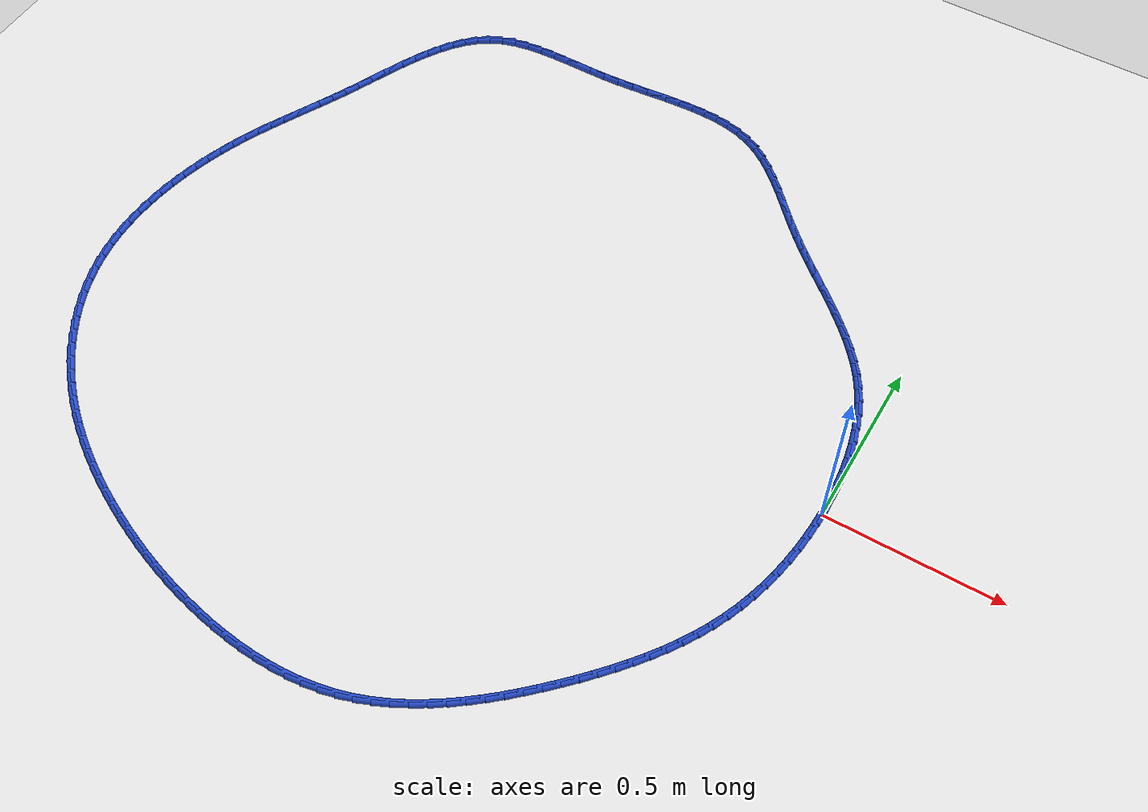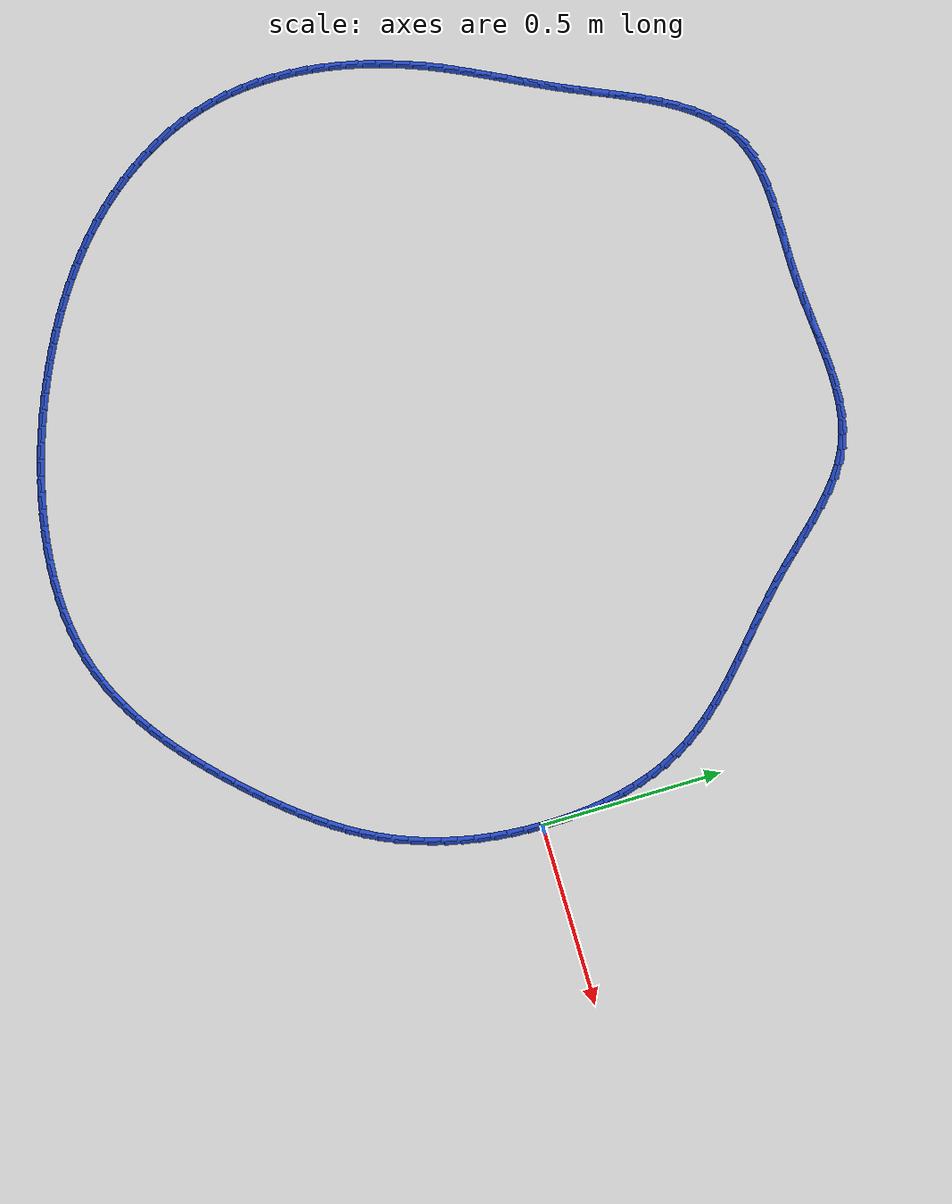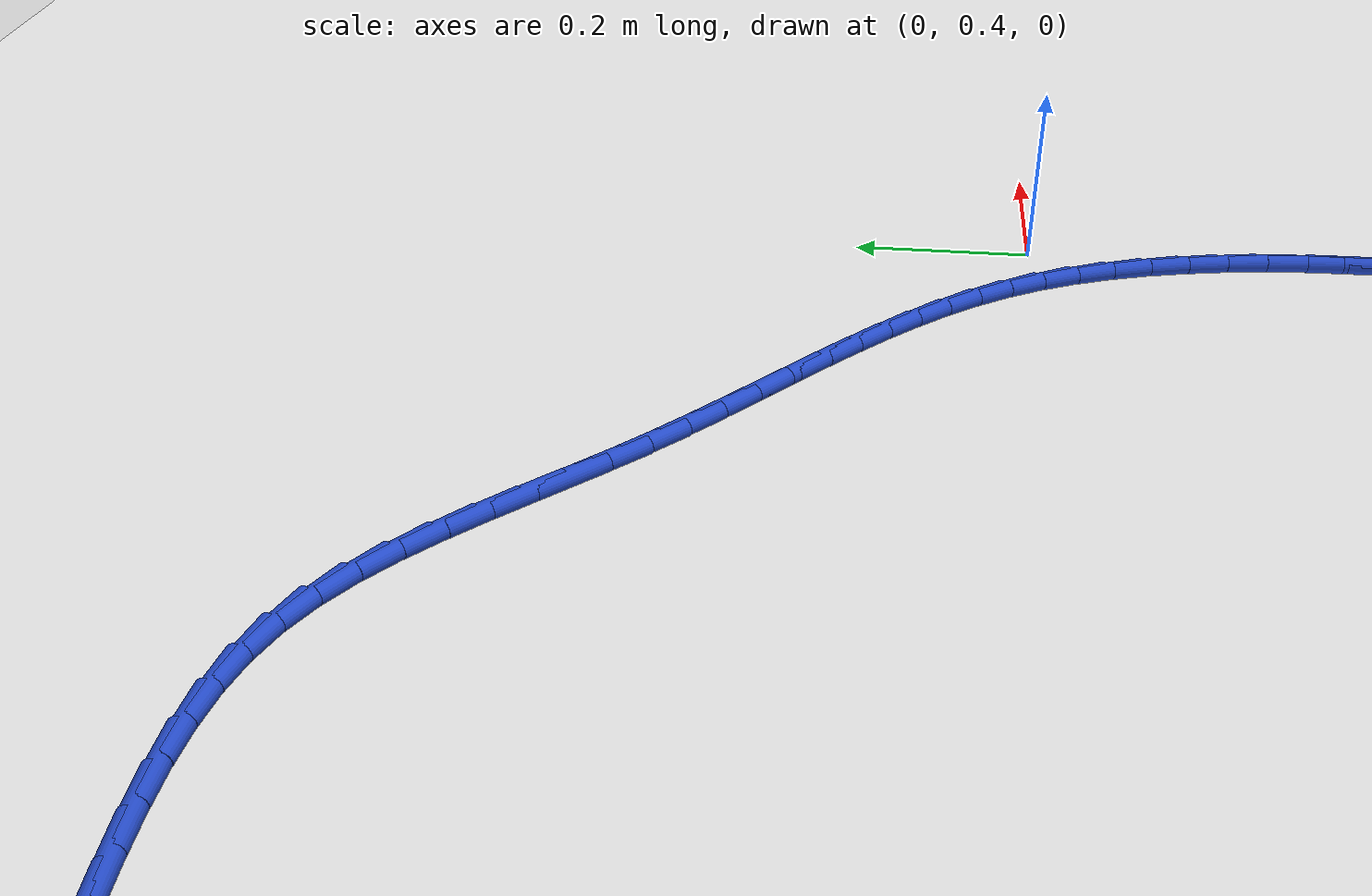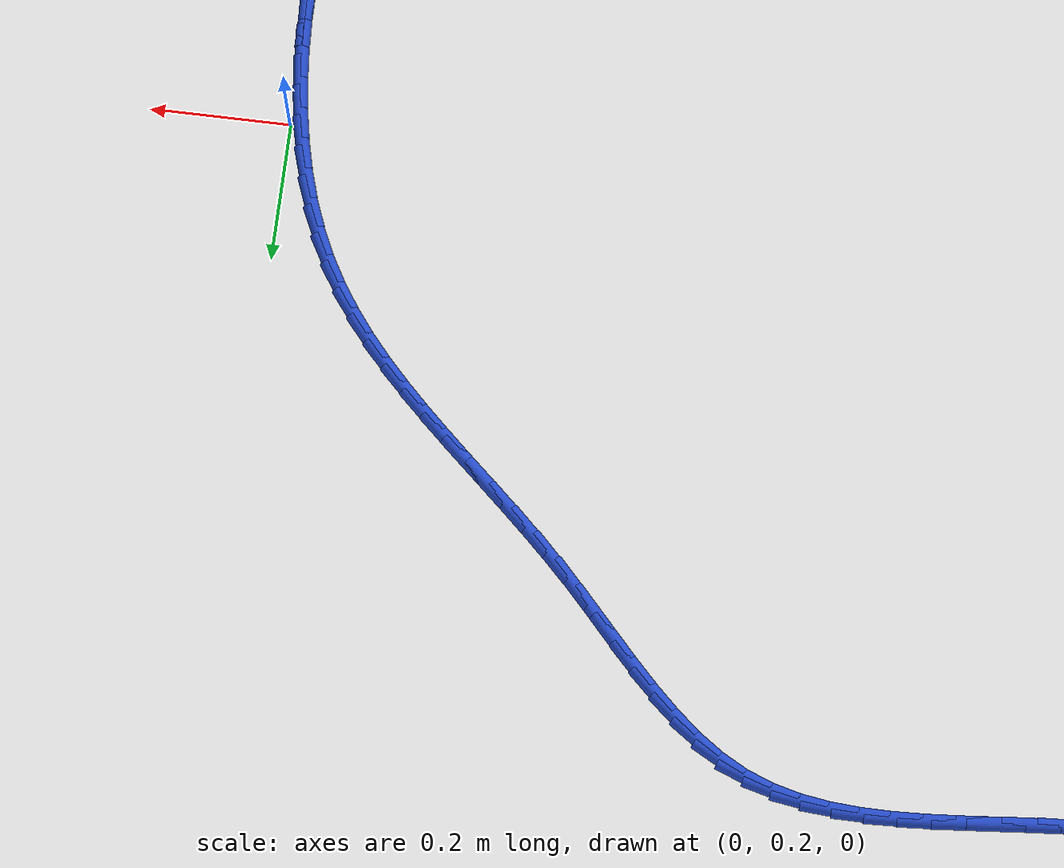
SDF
<sdf version="1.6">
 <world name="default">
  <light name="sun" type="directional">
   <pose>0 0 10 0 -0 0</pose>
   <diffuse>0.8 0.8 0.8 1</diffuse>
   <specular>0.2 0.2 0.2 1</specular>
   <attenuation>
    <range>1000</range>
    <constant>0.9</constant>
    <linear>0.01</linear>
    <quadratic>0.001</quadratic>
   </attenuation>
   <direction>-0.5 0.1 -0.9</direction>
  </light>
  <model name="ground_plane">
   <static>1</static>
   <link name="link">
    <collision name="collision">
     <geometry><plane><normal>0 0 1</normal><size>100 100</size></plane></geometry>
     <surface><friction><ode><mu>100</mu><mu2>50</mu2></ode></friction></surface>
    </collision>
    <visual name="visual">
     <cast_shadows>0</cast_shadows>
     <geometry><plane><normal>0 0 1</normal><size>100 100</size></plane></geometry>
     <material>
      <script><uri>file://media/materials/scripts/gazebo.material</uri><name>Gazebo/WhiteGlow</name></script>
     </material>
    </visual>
   </link>
  </model>
  <gravity>0 0 -9.8</gravity>
  <magnetic_field>6e-06 2.3e-05 -4.2e-05</magnetic_field>
  <atmosphere type="adiabatic"/>
  <physics name="default_physics" default="0" type="ode">
   <max_step_size>0.001</max_step_size>
   <real_time_factor>1</real_time_factor>
   <real_time_update_rate>1000</real_time_update_rate>
  </physics>
  <scene><ambient>0.4 0.4 0.4 1</ambient><background>0.7 0.7 0.7 1</background><shadows>1</shadows></scene>
  <spherical_coordinates>
   <surface_model>EARTH_WGS84</surface_model>
   <latitude_deg>0</latitude_deg>
   <longitude_deg>0</longitude_deg>
   <elevation>0</elevation>
   <heading_deg>0</heading_deg>
  </spherical_coordinates>
  <model name="line">
   <link name="link_0">
    <pose>0.0 -1.5265566588595902e-16 0.01 0 1.57 -1.5642455888296136</pose>
    <collision name="collision">
     <geometry><cylinder><radius>0.01</radius><length>0.08</length></cylinder></geometry>
    </collision>
    <visual name="visual">
     <material>
      <script><name>Gazebo/Blue</name><uri>file://media/materials/scripts/gazebo.material</uri></script>
     </material>
     <geometry><cylinder><radius>0.01</radius><length>0.08</length></cylinder></geometry>
    </visual>
   </link>
   <link name="link_1">
    <pose>-0.0003006945332461743 0.045901734075765366 0.01 0 1.57 -1.5239608890561258</pose>
    <collision name="collision">
     <geometry><cylinder><radius>0.01</radius><length>0.08</length></cylinder></geometry>
    </collision>
    <visual name="visual">
     <material>
      <script><name>Gazebo/Blue</name><uri>file://media/materials/scripts/gazebo.material</uri></script>
     </material>
     <geometry><cylinder><radius>0.01</radius><length>0.08</length></cylinder></geometry>
    </visual>
   </link>
   <link name="link_2">
    <pose>-0.0024520561953644262 0.09180262643703892 0.01 0 1.57 -1.480812491341075</pose>
    <collision name="collision">
     <geometry><cylinder><radius>0.01</radius><length>0.08</length></cylinder></geometry>
    </collision>
    <visual name="visual">
     <material>
      <script><name>Gazebo/Blue</name><uri>file://media/materials/scripts/gazebo.material</uri></script>
     </material>
     <geometry><cylinder><radius>0.01</radius><length>0.08</length></cylinder></geometry>
    </visual>
   </link>
   <link name="link_3">
    <pose>-0.006572178366805169 0.13746633713611803 0.01 0 1.57 -1.4342981341041827</pose>
    <collision name="collision">
     <geometry><cylinder><radius>0.01</radius><length>0.08</length></cylinder></geometry>
    </collision>
    <visual name="visual">
     <material>
      <script><name>Gazebo/Blue</name><uri>file://media/materials/scripts/gazebo.material</uri></script>
     </material>
     <geometry><cylinder><radius>0.01</radius><length>0.08</length></cylinder></geometry>
    </visual>
   </link>
   <link name="link_4">
    <pose>-0.012779154428018809 0.18265652622530024 0.01 0 1.57 -1.3838881149002507</pose>
    <collision name="collision">
     <geometry><cylinder><radius>0.01</radius><length>0.08</length></cylinder></geometry>
    </collision>
    <visual name="visual">
     <material>
      <script><name>Gazebo/Blue</name><uri>file://media/materials/scripts/gazebo.material</uri></script>
     </material>
     <geometry><cylinder><radius>0.01</radius><length>0.08</length></cylinder></geometry>
    </visual>
   </link>
   <link name="link_5">
    <pose>-0.02119107775945575 0.227136853756883 0.01 0 1.57 -1.329032156727063</pose>
    <collision name="collision">
     <geometry><cylinder><radius>0.01</radius><length>0.08</length></cylinder></geometry>
    </collision>
    <visual name="visual">
     <material>
      <script><name>Gazebo/Blue</name><uri>file://media/materials/scripts/gazebo.material</uri></script>
     </material>
     <geometry><cylinder><radius>0.01</radius><length>0.08</length></cylinder></geometry>
    </visual>
   </link>
   <link name="link_6">
    <pose>-0.03192604174156644 0.2706709797831639 0.01 0 1.57 -1.2691762153304145</pose>
    <collision name="collision">
     <geometry><cylinder><radius>0.01</radius><length>0.08</length></cylinder></geometry>
    </collision>
    <visual name="visual">
     <material>
      <script><name>Gazebo/Blue</name><uri>file://media/materials/scripts/gazebo.material</uri></script>
     </material>
     <geometry><cylinder><radius>0.01</radius><length>0.08</length></cylinder></geometry>
    </visual>
   </link>
   <link name="link_7">
    <pose>-0.04510213975480125 0.3130225643564404 0.01 0 1.57 -1.2037932281394</pose>
    <collision name="collision">
     <geometry><cylinder><radius>0.01</radius><length>0.08</length></cylinder></geometry>
    </collision>
    <visual name="visual">
     <material>
      <script><name>Gazebo/Blue</name><uri>file://media/materials/scripts/gazebo.material</uri></script>
     </material>
     <geometry><cylinder><radius>0.01</radius><length>0.08</length></cylinder></geometry>
    </visual>
   </link>
   <link name="link_8">
    <pose>-0.0608374651796106 0.35395526752901 0.01 0 1.57 -1.1324320763547209</pose>
    <collision name="collision">
     <geometry><cylinder><radius>0.01</radius><length>0.08</length></cylinder></geometry>
    </collision>
    <visual name="visual">
     <material>
      <script><name>Gazebo/Blue</name><uri>file://media/materials/scripts/gazebo.material</uri></script>
     </material>
     <geometry><cylinder><radius>0.01</radius><length>0.08</length></cylinder></geometry>
    </visual>
   </link>
   <link name="link_9">
    <pose>-0.07925011139644492 0.39323274935317043 0.01 0 1.57 -1.055426300103091</pose>
    <collision name="collision">
     <geometry><cylinder><radius>0.01</radius><length>0.08</length></cylinder></geometry>
    </collision>
    <visual name="visual">
     <material>
      <script><name>Gazebo/Blue</name><uri>file://media/materials/scripts/gazebo.material</uri></script>
     </material>
     <geometry><cylinder><radius>0.01</radius><length>0.08</length></cylinder></geometry>
    </visual>
   </link>
   <link name="link_10">
    <pose>-0.10043933438602108 0.43064110363823793 0.01 0 1.57 -0.9810597001686475</pose>
    <collision name="collision">
     <geometry><cylinder><radius>0.01</radius><length>0.08</length></cylinder></geometry>
    </collision>
    <visual name="visual">
     <material>
      <script><name>Gazebo/Blue</name><uri>file://media/materials/scripts/gazebo.material</uri></script>
     </material>
     <geometry><cylinder><radius>0.01</radius><length>0.08</length></cylinder></geometry>
    </visual>
   </link>
   <link name="link_11">
    <pose>-0.12426717433968576 0.4662489282256752 0.01 0 1.57 -0.9158500449054999</pose>
    <collision name="collision">
     <geometry><cylinder><radius>0.01</radius><length>0.08</length></cylinder></geometry>
    </collision>
    <visual name="visual">
     <material>
      <script><name>Gazebo/Blue</name><uri>file://media/materials/scripts/gazebo.material</uri></script>
     </material>
     <geometry><cylinder><radius>0.01</radius><length>0.08</length></cylinder></geometry>
    </visual>
   </link>
   <link name="link_12">
    <pose>-0.15043350243103995 0.5003179506028407 0.01 0 1.57 -0.8605735555581524</pose>
    <collision name="collision">
     <geometry><cylinder><radius>0.01</radius><length>0.08</length></cylinder></geometry>
    </collision>
    <visual name="visual">
     <material>
      <script><name>Gazebo/Blue</name><uri>file://media/materials/scripts/gazebo.material</uri></script>
     </material>
     <geometry><cylinder><radius>0.01</radius><length>0.08</length></cylinder></geometry>
    </visual>
   </link>
   <link name="link_13">
    <pose>-0.17863504573243025 0.5331136426169617 0.01 0 1.57 -0.8154330089115209</pose>
    <collision name="collision">
     <geometry><cylinder><radius>0.01</radius><length>0.08</length></cylinder></geometry>
    </collision>
    <visual name="visual">
     <material>
      <script><name>Gazebo/Blue</name><uri>file://media/materials/scripts/gazebo.material</uri></script>
     </material>
     <geometry><cylinder><radius>0.01</radius><length>0.08</length></cylinder></geometry>
    </visual>
   </link>
   <link name="link_14">
    <pose>-0.2085685313162034 0.5649014761152653 0.01 0 1.57 -0.7803233747333668</pose>
    <collision name="collision">
     <geometry><cylinder><radius>0.01</radius><length>0.08</length></cylinder></geometry>
    </collision>
    <visual name="visual">
     <material>
      <script><name>Gazebo/Blue</name><uri>file://media/materials/scripts/gazebo.material</uri></script>
     </material>
     <geometry><cylinder><radius>0.01</radius><length>0.08</length></cylinder></geometry>
    </visual>
   </link>
   <link name="link_15">
    <pose>-0.2399306862547059 0.5959469229449786 0.01 0 1.57 -0.754974021610793</pose>
    <collision name="collision">
     <geometry><cylinder><radius>0.01</radius><length>0.08</length></cylinder></geometry>
    </collision>
    <visual name="visual">
     <material>
      <script><name>Gazebo/Blue</name><uri>file://media/materials/scripts/gazebo.material</uri></script>
     </material>
     <geometry><cylinder><radius>0.01</radius><length>0.08</length></cylinder></geometry>
    </visual>
   </link>
   <link name="link_16">
    <pose>-0.27241823762028455 0.6265154549533289 0.01 0 1.57 -0.739055744368491</pose>
    <collision name="collision">
     <geometry><cylinder><radius>0.01</radius><length>0.08</length></cylinder></geometry>
    </collision>
    <visual name="visual">
     <material>
      <script><name>Gazebo/Blue</name><uri>file://media/materials/scripts/gazebo.material</uri></script>
     </material>
     <geometry><cylinder><radius>0.01</radius><length>0.08</length></cylinder></geometry>
    </visual>
   </link>
   <link name="link_17">
    <pose>-0.3057279124852858 0.6568725439875429 0.01 0 1.57 -0.732250464347682</pose>
    <collision name="collision">
     <geometry><cylinder><radius>0.01</radius><length>0.08</length></cylinder></geometry>
    </collision>
    <visual name="visual">
     <material>
      <script><name>Gazebo/Blue</name><uri>file://media/materials/scripts/gazebo.material</uri></script>
     </material>
     <geometry><cylinder><radius>0.01</radius><length>0.08</length></cylinder></geometry>
    </visual>
   </link>
   <link name="link_18">
    <pose>-0.33955643792205653 0.6872836618948482 0.01 0 1.57 -0.734288737815658</pose>
    <collision name="collision">
     <geometry><cylinder><radius>0.01</radius><length>0.08</length></cylinder></geometry>
    </collision>
    <visual name="visual">
     <material>
      <script><name>Gazebo/Blue</name><uri>file://media/materials/scripts/gazebo.material</uri></script>
     </material>
     <geometry><cylinder><radius>0.01</radius><length>0.08</length></cylinder></geometry>
    </visual>
   </link>
   <link name="link_19">
    <pose>-0.37360054100294326 0.7180142805224717 0.01 0 1.57 -0.7449615728654673</pose>
    <collision name="collision">
     <geometry><cylinder><radius>0.01</radius><length>0.08</length></cylinder></geometry>
    </collision>
    <visual name="visual">
     <material>
      <script><name>Gazebo/Blue</name><uri>file://media/materials/scripts/gazebo.material</uri></script>
     </material>
     <geometry><cylinder><radius>0.01</radius><length>0.08</length></cylinder></geometry>
    </visual>
   </link>
   <link name="link_20">
    <pose>-0.4075569488002925 0.7493298717176402 0.01 0 1.57 -0.7641116700986336</pose>
    <collision name="collision">
     <geometry><cylinder><radius>0.01</radius><length>0.08</length></cylinder></geometry>
    </collision>
    <visual name="visual">
     <material>
      <script><name>Gazebo/Blue</name><uri>file://media/materials/scripts/gazebo.material</uri></script>
     </material>
     <geometry><cylinder><radius>0.01</radius><length>0.08</length></cylinder></geometry>
    </visual>
   </link>
   <link name="link_21">
    <pose>-0.4411223883864512 0.7814959073275813 0.01 0 1.57 -0.7915079339891901</pose>
    <collision name="collision">
     <geometry><cylinder><radius>0.01</radius><length>0.08</length></cylinder></geometry>
    </collision>
    <visual name="visual">
     <material>
      <script><name>Gazebo/Blue</name><uri>file://media/materials/scripts/gazebo.material</uri></script>
     </material>
     <geometry><cylinder><radius>0.01</radius><length>0.08</length></cylinder></geometry>
    </visual>
   </link>
   <link name="link_22">
    <pose>-0.47399608903926926 0.8147737839711767 0.01 0 1.57 -0.8184175871909524</pose>
    <collision name="collision">
     <geometry><cylinder><radius>0.01</radius><length>0.08</length></cylinder></geometry>
    </collision>
    <visual name="visual">
     <material>
      <script><name>Gazebo/Blue</name><uri>file://media/materials/scripts/gazebo.material</uri></script>
     </material>
     <geometry><cylinder><radius>0.01</radius><length>0.08</length></cylinder></geometry>
    </visual>
   </link>
   <link name="link_23">
    <pose>-0.5060967165724656 0.8490675119576148 0.01 0 1.57 -0.8299045081256999</pose>
    <collision name="collision">
     <geometry><cylinder><radius>0.01</radius><length>0.08</length></cylinder></geometry>
    </collision>
    <visual name="visual">
     <material>
      <script><name>Gazebo/Blue</name><uri>file://media/materials/scripts/gazebo.material</uri></script>
     </material>
     <geometry><cylinder><radius>0.01</radius><length>0.08</length></cylinder></geometry>
    </visual>
   </link>
   <link name="link_24">
    <pose>-0.5377303510854071 0.8836501375621241 0.01 0 1.57 -0.8245276934373208</pose>
    <collision name="collision">
     <geometry><cylinder><radius>0.01</radius><length>0.08</length></cylinder></geometry>
    </collision>
    <visual name="visual">
     <material>
      <script><name>Gazebo/Blue</name><uri>file://media/materials/scripts/gazebo.material</uri></script>
     </material>
     <geometry><cylinder><radius>0.01</radius><length>0.08</length></cylinder></geometry>
    </visual>
   </link>
   <link name="link_25">
    <pose>-0.5692426123155785 0.9177303106489254 0.01 0 1.57 -0.8016678981493165</pose>
    <collision name="collision">
     <geometry><cylinder><radius>0.01</radius><length>0.08</length></cylinder></geometry>
    </collision>
    <visual name="visual">
     <material>
      <script><name>Gazebo/Blue</name><uri>file://media/materials/scripts/gazebo.material</uri></script>
     </material>
     <geometry><cylinder><radius>0.01</radius><length>0.08</length></cylinder></geometry>
    </visual>
   </link>
   <link name="link_26">
    <pose>-0.6009791200004649 0.9505166810822406 0.01 0 1.57 -0.7599280719795295</pose>
    <collision name="collision">
     <geometry><cylinder><radius>0.01</radius><length>0.08</length></cylinder></geometry>
    </collision>
    <visual name="visual">
     <material>
      <script><name>Gazebo/Blue</name><uri>file://media/materials/scripts/gazebo.material</uri></script>
     </material>
     <geometry><cylinder><radius>0.01</radius><length>0.08</length></cylinder></geometry>
    </visual>
   </link>
   <link name="link_27">
    <pose>-0.6332854938775516 0.9812178987262915 0.01 0 1.57 -0.6972171529305797</pose>
    <collision name="collision">
     <geometry><cylinder><radius>0.01</radius><length>0.08</length></cylinder></geometry>
    </collision>
    <visual name="visual">
     <material>
      <script><name>Gazebo/Blue</name><uri>file://media/materials/scripts/gazebo.material</uri></script>
     </material>
     <geometry><cylinder><radius>0.01</radius><length>0.08</length></cylinder></geometry>
    </visual>
   </link>
   <link name="link_28">
    <pose>-0.666507353684323 1.009042613445299 0.01 0 1.57 -0.6110914988036711</pose>
    <collision name="collision">
     <geometry><cylinder><radius>0.01</radius><length>0.08</length></cylinder></geometry>
    </collision>
    <visual name="visual">
     <material>
      <script><name>Gazebo/Blue</name><uri>file://media/materials/scripts/gazebo.material</uri></script>
     </material>
     <geometry><cylinder><radius>0.01</radius><length>0.08</length></cylinder></geometry>
    </visual>
   </link>
   <link name="link_29">
    <pose>-0.7009903191582645 1.0331994751034852 0.01 0 1.57 -0.4996109202684271</pose>
    <collision name="collision">
     <geometry><cylinder><radius>0.01</radius><length>0.08</length></cylinder></geometry>
    </collision>
    <visual name="visual">
     <material>
      <script><name>Gazebo/Blue</name><uri>file://media/materials/scripts/gazebo.material</uri></script>
     </material>
     <geometry><cylinder><radius>0.01</radius><length>0.08</length></cylinder></geometry>
    </visual>
   </link>
   <link name="link_30">
    <pose>-0.7370800097640913 1.0528971343306763 0.01 0 1.57 -0.3694298204295683</pose>
    <collision name="collision">
     <geometry><cylinder><radius>0.01</radius><length>0.08</length></cylinder></geometry>
    </collision>
    <visual name="visual">
     <material>
      <script><name>Gazebo/Blue</name><uri>file://media/materials/scripts/gazebo.material</uri></script>
     </material>
     <geometry><cylinder><radius>0.01</radius><length>0.08</length></cylinder></geometry>
    </visual>
   </link>
   <link name="link_31">
    <pose>-0.7750334260151597 1.0675929760785206 0.01 0 1.57 -0.2489895725936515</pose>
    <collision name="collision">
     <geometry><cylinder><radius>0.01</radius><length>0.08</length></cylinder></geometry>
    </collision>
    <visual name="visual">
     <material>
      <script><name>Gazebo/Blue</name><uri>file://media/materials/scripts/gazebo.material</uri></script>
     </material>
     <geometry><cylinder><radius>0.01</radius><length>0.08</length></cylinder></geometry>
    </visual>
   </link>
   <link name="link_32">
    <pose>-0.8147684435773628 1.0776962357511082 0.01 0 1.57 -0.14757851697039848</pose>
    <collision name="collision">
     <geometry><cylinder><radius>0.01</radius><length>0.08</length></cylinder></geometry>
    </collision>
    <visual name="visual">
     <material>
      <script><name>Gazebo/Blue</name><uri>file://media/materials/scripts/gazebo.material</uri></script>
     </material>
     <geometry><cylinder><radius>0.01</radius><length>0.08</length></cylinder></geometry>
    </visual>
   </link>
   <link name="link_33">
    <pose>-0.8561218298339164 1.083843802243982 0.01 0 1.57 -0.06598349007495755</pose>
    <collision name="collision">
     <geometry><cylinder><radius>0.01</radius><length>0.08</length></cylinder></geometry>
    </collision>
    <visual name="visual">
     <material>
      <script><name>Gazebo/Blue</name><uri>file://media/materials/scripts/gazebo.material</uri></script>
     </material>
     <geometry><cylinder><radius>0.01</radius><length>0.08</length></cylinder></geometry>
    </visual>
   </link>
   <link name="link_34">
    <pose>-0.8989303521680363 1.0866725644526858 0.01 0 1.57 -0.0033298154087916683</pose>
    <collision name="collision">
     <geometry><cylinder><radius>0.01</radius><length>0.08</length></cylinder></geometry>
    </collision>
    <visual name="visual">
     <material>
      <script><name>Gazebo/Blue</name><uri>file://media/materials/scripts/gazebo.material</uri></script>
     </material>
     <geometry><cylinder><radius>0.01</radius><length>0.08</length></cylinder></geometry>
    </visual>
   </link>
   <link name="link_35">
    <pose>-0.9430307779629375 1.086819411272762 0.01 0 1.57 0.041943495557022384</pose>
    <collision name="collision">
     <geometry><cylinder><radius>0.01</radius><length>0.08</length></cylinder></geometry>
    </collision>
    <visual name="visual">
     <material>
      <script><name>Gazebo/Blue</name><uri>file://media/materials/scripts/gazebo.material</uri></script>
     </material>
     <geometry><cylinder><radius>0.01</radius><length>0.08</length></cylinder></geometry>
    </visual>
   </link>
   <link name="link_36">
    <pose>-0.9882598746018367 1.084921231599755 0.01 0 1.57 0.07145193034690786</pose>
    <collision name="collision">
     <geometry><cylinder><radius>0.01</radius><length>0.08</length></cylinder></geometry>
    </collision>
    <visual name="visual">
     <material>
      <script><name>Gazebo/Blue</name><uri>file://media/materials/scripts/gazebo.material</uri></script>
     </material>
     <geometry><cylinder><radius>0.01</radius><length>0.08</length></cylinder></geometry>
    </visual>
   </link>
   <link name="link_37">
    <pose>-1.0344544094679489 1.081614914329207 0.01 0 1.57 0.08654600794670991</pose>
    <collision name="collision">
     <geometry><cylinder><radius>0.01</radius><length>0.08</length></cylinder></geometry>
    </collision>
    <visual name="visual">
     <material>
      <script><name>Gazebo/Blue</name><uri>file://media/materials/scripts/gazebo.material</uri></script>
     </material>
     <geometry><cylinder><radius>0.01</radius><length>0.08</length></cylinder></geometry>
    </visual>
   </link>
   <link name="link_38">
    <pose>-1.0814511499444899 1.0775373483566624 0.01 0 1.57 0.0881901494907465</pose>
    <collision name="collision">
     <geometry><cylinder><radius>0.01</radius><length>0.08</length></cylinder></geometry>
    </collision>
    <visual name="visual">
     <material>
      <script><name>Gazebo/Blue</name><uri>file://media/materials/scripts/gazebo.material</uri></script>
     </material>
     <geometry><cylinder><radius>0.01</radius><length>0.08</length></cylinder></geometry>
    </visual>
   </link>
   <link name="link_39">
    <pose>-1.1290868634146751 1.0733254225776638 0.01 0 1.57 0.07694784559035789</pose>
    <collision name="collision">
     <geometry><cylinder><radius>0.01</radius><length>0.08</length></cylinder></geometry>
    </collision>
    <visual name="visual">
     <material>
      <script><name>Gazebo/Blue</name><uri>file://media/materials/scripts/gazebo.material</uri></script>
     </material>
     <geometry><cylinder><radius>0.01</radius><length>0.08</length></cylinder></geometry>
    </visual>
   </link>
   <link name="link_40">
    <pose>-1.1771983172617206 1.0696160258877545 0.01 0 1.57 0.05302271331929114</pose>
    <collision name="collision">
     <geometry><cylinder><radius>0.01</radius><length>0.08</length></cylinder></geometry>
    </collision>
    <visual name="visual">
     <material>
      <script><name>Gazebo/Blue</name><uri>file://media/materials/scripts/gazebo.material</uri></script>
     </material>
     <geometry><cylinder><radius>0.01</radius><length>0.08</length></cylinder></geometry>
    </visual>
   </link>
   <link name="link_41">
    <pose>-1.2256222788688422 1.067046047182478 0.01 0 1.57 0.020469968103375757</pose>
    <collision name="collision">
     <geometry><cylinder><radius>0.01</radius><length>0.08</length></cylinder></geometry>
    </collision>
    <visual name="visual">
     <material>
      <script><name>Gazebo/Blue</name><uri>file://media/materials/scripts/gazebo.material</uri></script>
     </material>
     <geometry><cylinder><radius>0.01</radius><length>0.08</length></cylinder></geometry>
    </visual>
   </link>
   <link name="link_42">
    <pose>-1.2741656100175798 1.0660522279284406 0.01 0 1.57 -0.00043402135909211773</pose>
    <collision name="collision">
     <geometry><cylinder><radius>0.01</radius><length>0.08</length></cylinder></geometry>
    </collision>
    <visual name="visual">
     <material>
      <script><name>Gazebo/Blue</name><uri>file://media/materials/scripts/gazebo.material</uri></script>
     </material>
     <geometry><cylinder><radius>0.01</radius><length>0.08</length></cylinder></geometry>
    </visual>
   </link>
   <link name="link_43">
    <pose>-1.322486037088437 1.0660732000271866 0.01 0 1.57 -0.0034349697633158185</pose>
    <collision name="collision">
     <geometry><cylinder><radius>0.01</radius><length>0.08</length></cylinder></geometry>
    </collision>
    <visual name="visual">
     <material>
      <script><name>Gazebo/Blue</name><uri>file://media/materials/scripts/gazebo.material</uri></script>
     </material>
     <geometry><cylinder><radius>0.01</radius><length>0.08</length></cylinder></geometry>
    </visual>
   </link>
   <link name="link_44">
    <pose>-1.3701948897877358 1.0662370791381892 0.01 0 1.57 0.012099905925100116</pose>
    <collision name="collision">
     <geometry><cylinder><radius>0.01</radius><length>0.08</length></cylinder></geometry>
    </collision>
    <visual name="visual">
     <material>
      <script><name>Gazebo/Blue</name><uri>file://media/materials/scripts/gazebo.material</uri></script>
     </material>
     <geometry><cylinder><radius>0.01</radius><length>0.08</length></cylinder></geometry>
    </visual>
   </link>
   <link name="link_45">
    <pose>-1.4169034830368563 1.065671881970635 0.01 0 1.57 0.047763149986099145</pose>
    <collision name="collision">
     <geometry><cylinder><radius>0.01</radius><length>0.08</length></cylinder></geometry>
    </collision>
    <visual name="visual">
     <material>
      <script><name>Gazebo/Blue</name><uri>file://media/materials/scripts/gazebo.material</uri></script>
     </material>
     <geometry><cylinder><radius>0.01</radius><length>0.08</length></cylinder></geometry>
    </visual>
   </link>
   <link name="link_46">
    <pose>-1.4622231317571772 1.0635056252337116 0.01 0 1.57 0.10614717876251863</pose>
    <collision name="collision">
     <geometry><cylinder><radius>0.01</radius><length>0.08</length></cylinder></geometry>
    </collision>
    <visual name="visual">
     <material>
      <script><name>Gazebo/Blue</name><uri>file://media/materials/scripts/gazebo.material</uri></script>
     </material>
     <geometry><cylinder><radius>0.01</radius><length>0.08</length></cylinder></geometry>
    </visual>
   </link>
   <link name="link_47">
    <pose>-1.5057651508700798 1.0588663256366069 0.01 0 1.57 0.19062820335646008</pose>
    <collision name="collision">
     <geometry><cylinder><radius>0.01</radius><length>0.08</length></cylinder></geometry>
    </collision>
    <visual name="visual">
     <material>
      <script><name>Gazebo/Blue</name><uri>file://media/materials/scripts/gazebo.material</uri></script>
     </material>
     <geometry><cylinder><radius>0.01</radius><length>0.08</length></cylinder></geometry>
    </visual>
   </link>
   <link name="link_48">
    <pose>-1.5471408552969441 1.050881999888508 0.01 0 1.57 0.3045235966203885</pose>
    <collision name="collision">
     <geometry><cylinder><radius>0.01</radius><length>0.08</length></cylinder></geometry>
    </collision>
    <visual name="visual">
     <material>
      <script><name>Gazebo/Blue</name><uri>file://media/materials/scripts/gazebo.material</uri></script>
     </material>
     <geometry><cylinder><radius>0.01</radius><length>0.08</length></cylinder></geometry>
    </visual>
   </link>
   <link name="link_49">
    <pose>-1.58596155995915 1.0386806646986027 0.01 0 1.57 0.44904205229613137</pose>
    <collision name="collision">
     <geometry><cylinder><radius>0.01</radius><length>0.08</length></cylinder></geometry>
    </collision>
    <visual name="visual">
     <material>
      <script><name>Gazebo/Blue</name><uri>file://media/materials/scripts/gazebo.material</uri></script>
     </material>
     <geometry><cylinder><radius>0.01</radius><length>0.08</length></cylinder></geometry>
    </visual>
   </link>
   <link name="link_50">
    <pose>-1.6218393976123193 1.0213920627354787 0.01 0 1.57 0.6086790457043356</pose>
    <collision name="collision">
     <geometry><cylinder><radius>0.01</radius><length>0.08</length></cylinder></geometry>
    </collision>
    <visual name="visual">
     <material>
      <script><name>Gazebo/Blue</name><uri>file://media/materials/scripts/gazebo.material</uri></script>
     </material>
     <geometry><cylinder><radius>0.01</radius><length>0.08</length></cylinder></geometry>
    </visual>
   </link>
   <link name="link_51">
    <pose>-1.6545867881548593 0.9985686231480351 0.01 0 1.57 0.7497780026498171</pose>
    <collision name="collision">
     <geometry><cylinder><radius>0.01</radius><length>0.08</length></cylinder></geometry>
    </collision>
    <visual name="visual">
     <material>
      <script><name>Gazebo/Blue</name><uri>file://media/materials/scripts/gazebo.material</uri></script>
     </material>
     <geometry><cylinder><radius>0.01</radius><length>0.08</length></cylinder></geometry>
    </visual>
   </link>
   <link name="link_52">
    <pose>-1.6844770159355724 0.9707353845583916 0.01 0 1.57 0.8660047691046775</pose>
    <collision name="collision">
     <geometry><cylinder><radius>0.01</radius><length>0.08</length></cylinder></geometry>
    </collision>
    <visual name="visual">
     <material>
      <script><name>Gazebo/Blue</name><uri>file://media/materials/scripts/gazebo.material</uri></script>
     </material>
     <geometry><cylinder><radius>0.01</radius><length>0.08</length></cylinder></geometry>
    </visual>
   </link>
   <link name="link_53">
    <pose>-1.711847951943183 0.9385536893929116 0.01 0 1.57 0.9585498688544589</pose>
    <collision name="collision">
     <geometry><cylinder><radius>0.01</radius><length>0.08</length></cylinder></geometry>
    </collision>
    <visual name="visual">
     <material>
      <script><name>Gazebo/Blue</name><uri>file://media/materials/scripts/gazebo.material</uri></script>
     </material>
     <geometry><cylinder><radius>0.01</radius><length>0.08</length></cylinder></geometry>
    </visual>
   </link>
   <link name="link_54">
    <pose>-1.737037467166414 0.9026848800779569 0.01 0 1.57 1.030202602927615</pose>
    <collision name="collision">
     <geometry><cylinder><radius>0.01</radius><length>0.08</length></cylinder></geometry>
    </collision>
    <visual name="visual">
     <material>
      <script><name>Gazebo/Blue</name><uri>file://media/materials/scripts/gazebo.material</uri></script>
     </material>
     <geometry><cylinder><radius>0.01</radius><length>0.08</length></cylinder></geometry>
    </visual>
   </link>
   <link name="link_55">
    <pose>-1.7603834325939864 0.8637902990398908 0.01 0 1.57 1.0839485673946732</pose>
    <collision name="collision">
     <geometry><cylinder><radius>0.01</radius><length>0.08</length></cylinder></geometry>
    </collision>
    <visual name="visual">
     <material>
      <script><name>Gazebo/Blue</name><uri>file://media/materials/scripts/gazebo.material</uri></script>
     </material>
     <geometry><cylinder><radius>0.01</radius><length>0.08</length></cylinder></geometry>
    </visual>
   </link>
   <link name="link_56">
    <pose>-1.7822237192146237 0.8225312887050757 0.01 0 1.57 1.1223181926764925</pose>
    <collision name="collision">
     <geometry><cylinder><radius>0.01</radius><length>0.08</length></cylinder></geometry>
    </collision>
    <visual name="visual">
     <material>
      <script><name>Gazebo/Blue</name><uri>file://media/materials/scripts/gazebo.material</uri></script>
     </material>
     <geometry><cylinder><radius>0.01</radius><length>0.08</length></cylinder></geometry>
    </visual>
   </link>
   <link name="link_57">
    <pose>-1.8028961980170493 0.7795691914998744 0.01 0 1.57 1.1471713649403947</pose>
    <collision name="collision">
     <geometry><cylinder><radius>0.01</radius><length>0.08</length></cylinder></geometry>
    </collision>
    <visual name="visual">
     <material>
      <script><name>Gazebo/Blue</name><uri>file://media/materials/scripts/gazebo.material</uri></script>
     </material>
     <geometry><cylinder><radius>0.01</radius><length>0.08</length></cylinder></geometry>
    </visual>
   </link>
   <link name="link_58">
    <pose>-1.8227387399899864 0.735565349850649 0.01 0 1.57 1.159665550981344</pose>
    <collision name="collision">
     <geometry><cylinder><radius>0.01</radius><length>0.08</length></cylinder></geometry>
    </collision>
    <visual name="visual">
     <material>
      <script><name>Gazebo/Blue</name><uri>file://media/materials/scripts/gazebo.material</uri></script>
     </material>
     <geometry><cylinder><radius>0.01</radius><length>0.08</length></cylinder></geometry>
    </visual>
   </link>
   <link name="link_59">
    <pose>-1.8420892161221556 0.6911811061837627 0.01 0 1.57 1.1602698970088359</pose>
    <collision name="collision">
     <geometry><cylinder><radius>0.01</radius><length>0.08</length></cylinder></geometry>
    </collision>
    <visual name="visual">
     <material>
      <script><name>Gazebo/Blue</name><uri>file://media/materials/scripts/gazebo.material</uri></script>
     </material>
     <geometry><cylinder><radius>0.01</radius><length>0.08</length></cylinder></geometry>
    </visual>
   </link>
   <link name="link_60">
    <pose>-1.8612854974022817 0.6470778029255781 0.01 0 1.57 1.1487971476209038</pose>
    <collision name="collision">
     <geometry><cylinder><radius>0.01</radius><length>0.08</length></cylinder></geometry>
    </collision>
    <visual name="visual">
     <material>
      <script><name>Gazebo/Blue</name><uri>file://media/materials/scripts/gazebo.material</uri></script>
     </material>
     <geometry><cylinder><radius>0.01</radius><length>0.08</length></cylinder></geometry>
    </visual>
   </link>
   <link name="link_61">
    <pose>-1.8806644361677238 0.6039149452864928 0.01 0 1.57 1.1300412278332865</pose>
    <collision name="collision">
     <geometry><cylinder><radius>0.01</radius><length>0.08</length></cylinder></geometry>
    </collision>
    <visual name="visual">
     <material>
      <script><name>Gazebo/Blue</name><uri>file://media/materials/scripts/gazebo.material</uri></script>
     </material>
     <geometry><cylinder><radius>0.01</radius><length>0.08</length></cylinder></geometry>
    </visual>
   </link>
   <link name="link_62">
    <pose>-1.9004045233549984 0.5620664215282591 0.01 0 1.57 1.1155306119053663</pose>
    <collision name="collision">
     <geometry><cylinder><radius>0.01</radius><length>0.08</length></cylinder></geometry>
    </collision>
    <visual name="visual">
     <material>
      <script><name>Gazebo/Blue</name><uri>file://media/materials/scripts/gazebo.material</uri></script>
     </material>
     <geometry><cylinder><radius>0.01</radius><length>0.08</length></cylinder></geometry>
    </visual>
   </link>
   <link name="link_63">
    <pose>-1.920355724410357 0.5213135989600497 0.01 0 1.57 1.1072143394008402</pose>
    <collision name="collision">
     <geometry><cylinder><radius>0.01</radius><length>0.08</length></cylinder></geometry>
    </collision>
    <visual name="visual">
     <material>
      <script><name>Gazebo/Blue</name><uri>file://media/materials/scripts/gazebo.material</uri></script>
     </material>
     <geometry><cylinder><radius>0.01</radius><length>0.08</length></cylinder></geometry>
    </visual>
   </link>
   <link name="link_64">
    <pose>-1.9403271589323747 0.48136417626777095 0.01 0 1.57 1.1054943284828938</pose>
    <collision name="collision">
     <geometry><cylinder><radius>0.01</radius><length>0.08</length></cylinder></geometry>
    </collision>
    <visual name="visual">
     <material>
      <script><name>Gazebo/Blue</name><uri>file://media/materials/scripts/gazebo.material</uri></script>
     </material>
     <geometry><cylinder><radius>0.01</radius><length>0.08</length></cylinder></geometry>
    </visual>
   </link>
   <link name="link_65">
    <pose>-1.9601279465196264 0.44192585213733065 0.01 0 1.57 1.110632686682203</pose>
    <collision name="collision">
     <geometry><cylinder><radius>0.01</radius><length>0.08</length></cylinder></geometry>
    </collision>
    <visual name="visual">
     <material>
      <script><name>Gazebo/Blue</name><uri>file://media/materials/scripts/gazebo.material</uri></script>
     </material>
     <geometry><cylinder><radius>0.01</radius><length>0.08</length></cylinder></geometry>
    </visual>
   </link>
   <link name="link_66">
    <pose>-1.979567206770688 0.4027063252546359 0.01 0 1.57 1.1227346157262308</pose>
    <collision name="collision">
     <geometry><cylinder><radius>0.01</radius><length>0.08</length></cylinder></geometry>
    </collision>
    <visual name="visual">
     <material>
      <script><name>Gazebo/Blue</name><uri>file://media/materials/scripts/gazebo.material</uri></script>
     </material>
     <geometry><cylinder><radius>0.01</radius><length>0.08</length></cylinder></geometry>
    </visual>
   </link>
   <link name="link_67">
    <pose>-1.9984540592841333 0.36341329430559355 0.01 0 1.57 1.1417302962480769</pose>
    <collision name="collision">
     <geometry><cylinder><radius>0.01</radius><length>0.08</length></cylinder></geometry>
    </collision>
    <visual name="visual">
     <material>
      <script><name>Gazebo/Blue</name><uri>file://media/materials/scripts/gazebo.material</uri></script>
     </material>
     <geometry><cylinder><radius>0.01</radius><length>0.08</length></cylinder></geometry>
    </visual>
   </link>
   <link name="link_68">
    <pose>-2.016597623658538 0.3237544579761116 0.01 0 1.57 1.1673574761366174</pose>
    <collision name="collision">
     <geometry><cylinder><radius>0.01</radius><length>0.08</length></cylinder></geometry>
    </collision>
    <visual name="visual">
     <material>
      <script><name>Gazebo/Blue</name><uri>file://media/materials/scripts/gazebo.material</uri></script>
     </material>
     <geometry><cylinder><radius>0.01</radius><length>0.08</length></cylinder></geometry>
    </visual>
   </link>
   <link name="link_69">
    <pose>-2.0338070194924764 0.28343751495209696 0.01 0 1.57 1.1989408204281315</pose>
    <collision name="collision">
     <geometry><cylinder><radius>0.01</radius><length>0.08</length></cylinder></geometry>
    </collision>
    <visual name="visual">
     <material>
      <script><name>Gazebo/Blue</name><uri>file://media/materials/scripts/gazebo.material</uri></script>
     </material>
     <geometry><cylinder><radius>0.01</radius><length>0.08</length></cylinder></geometry>
    </visual>
   </link>
   <link name="link_70">
    <pose>-2.0498940034449307 0.242188769001571 0.01 0 1.57 1.2333861281324308</pose>
    <collision name="collision">
     <geometry><cylinder><radius>0.01</radius><length>0.08</length></cylinder></geometry>
    </collision>
    <visual name="visual">
     <material>
      <script><name>Gazebo/Blue</name><uri>file://media/materials/scripts/gazebo.material</uri></script>
     </material>
     <geometry><cylinder><radius>0.01</radius><length>0.08</length></cylinder></geometry>
    </visual>
   </link>
   <link name="link_71">
    <pose>-2.0647042041639168 0.19997349875098955 0.01 0 1.57 1.2689880031820608</pose>
    <collision name="collision">
     <geometry><cylinder><radius>0.01</radius><length>0.08</length></cylinder></geometry>
    </collision>
    <visual name="visual">
     <material>
      <script><name>Gazebo/Blue</name><uri>file://media/materials/scripts/gazebo.material</uri></script>
     </material>
     <geometry><cylinder><radius>0.01</radius><length>0.08</length></cylinder></geometry>
    </visual>
   </link>
   <link name="link_72">
    <pose>-2.0781067341207735 0.1569226667300592 0.01 0 1.57 1.3059903645979478</pose>
    <collision name="collision">
     <geometry><cylinder><radius>0.01</radius><length>0.08</length></cylinder></geometry>
    </collision>
    <visual name="visual">
     <material>
      <script><name>Gazebo/Blue</name><uri>file://media/materials/scripts/gazebo.material</uri></script>
     </material>
     <geometry><cylinder><radius>0.01</radius><length>0.08</length></cylinder></geometry>
    </visual>
   </link>
   <link name="link_73">
    <pose>-2.0899711774406478 0.11317056309715195 0.01 0 1.57 1.344673266465697</pose>
    <collision name="collision">
     <geometry><cylinder><radius>0.01</radius><length>0.08</length></cylinder></geometry>
    </collision>
    <visual name="visual">
     <material>
      <script><name>Gazebo/Blue</name><uri>file://media/materials/scripts/gazebo.material</uri></script>
     </material>
     <geometry><cylinder><radius>0.01</radius><length>0.08</length></cylinder></geometry>
    </visual>
   </link>
   <link name="link_74">
    <pose>-2.1001671182486845 0.06885147801064018 0.01 0 1.57 1.3853174714504881</pose>
    <collision name="collision">
     <geometry><cylinder><radius>0.01</radius><length>0.08</length></cylinder></geometry>
    </collision>
    <visual name="visual">
     <material>
      <script><name>Gazebo/Blue</name><uri>file://media/materials/scripts/gazebo.material</uri></script>
     </material>
     <geometry><cylinder><radius>0.01</radius><length>0.08</length></cylinder></geometry>
    </visual>
   </link>
   <link name="link_75">
    <pose>-2.1085641406700293 0.02409970162889607 0.01 0 1.57 1.4282043486091807</pose>
    <collision name="collision">
     <geometry><cylinder><radius>0.01</radius><length>0.08</length></cylinder></geometry>
    </collision>
    <visual name="visual">
     <material>
      <script><name>Gazebo/Blue</name><uri>file://media/materials/scripts/gazebo.material</uri></script>
     </material>
     <geometry><cylinder><radius>0.01</radius><length>0.08</length></cylinder></geometry>
    </visual>
   </link>
   <link name="link_76">
    <pose>-2.1150318288298293 -0.020950475889708386 0.01 0 1.57 1.4736135003460378</pose>
    <collision name="collision">
     <geometry><cylinder><radius>0.01</radius><length>0.08</length></cylinder></geometry>
    </collision>
    <visual name="visual">
     <material>
      <script><name>Gazebo/Blue</name><uri>file://media/materials/scripts/gazebo.material</uri></script>
     </material>
     <geometry><cylinder><radius>0.01</radius><length>0.08</length></cylinder></geometry>
    </visual>
   </link>
   <link name="link_77">
    <pose>-2.119439766853229 -0.06616476438680052 0.01 0 1.57 1.5218176122886777</pose>
    <collision name="collision">
     <geometry><cylinder><radius>0.01</radius><length>0.08</length></cylinder></geometry>
    </collision>
    <visual name="visual">
     <material>
      <script><name>Gazebo/Blue</name><uri>file://media/materials/scripts/gazebo.material</uri></script>
     </material>
     <geometry><cylinder><radius>0.01</radius><length>0.08</length></cylinder></geometry>
    </visual>
   </link>
   <link name="link_78">
    <pose>-2.121657538865375 -0.1114088737040072 0.01 0 1.57 -1.5685187345004907</pose>
    <collision name="collision">
     <geometry><cylinder><radius>0.01</radius><length>0.08</length></cylinder></geometry>
    </collision>
    <visual name="visual">
     <material>
      <script><name>Gazebo/Blue</name><uri>file://media/materials/scripts/gazebo.material</uri></script>
     </material>
     <geometry><cylinder><radius>0.01</radius><length>0.08</length></cylinder></geometry>
    </visual>
   </link>
   <link name="link_79">
    <pose>-2.1215547289914136 -0.1565485136829578 0.01 0 1.57 -1.513980978570573</pose>
    <collision name="collision">
     <geometry><cylinder><radius>0.01</radius><length>0.08</length></cylinder></geometry>
    </collision>
    <visual name="visual">
     <material>
      <script><name>Gazebo/Blue</name><uri>file://media/materials/scripts/gazebo.material</uri></script>
     </material>
     <geometry><cylinder><radius>0.01</radius><length>0.08</length></cylinder></geometry>
    </visual>
   </link>
   <link name="link_80">
    <pose>-2.119000921356489 -0.20144939416527835 0.01 0 1.57 -1.4559774639001841</pose>
    <collision name="collision">
     <geometry><cylinder><radius>0.01</radius><length>0.08</length></cylinder></geometry>
    </collision>
    <visual name="visual">
     <material>
      <script><name>Gazebo/Blue</name><uri>file://media/materials/scripts/gazebo.material</uri></script>
     </material>
     <geometry><cylinder><radius>0.01</radius><length>0.08</length></cylinder></geometry>
    </visual>
   </link>
   <link name="link_81">
    <pose>-2.1138657000857486 -0.24597722499259808 0.01 0 1.57 -1.394390215223277</pose>
    <collision name="collision">
     <geometry><cylinder><radius>0.01</radius><length>0.08</length></cylinder></geometry>
    </collision>
    <visual name="visual">
     <material>
      <script><name>Gazebo/Blue</name><uri>file://media/materials/scripts/gazebo.material</uri></script>
     </material>
     <geometry><cylinder><radius>0.01</radius><length>0.08</length></cylinder></geometry>
    </visual>
   </link>
   <link name="link_82">
    <pose>-2.1060186493043385 -0.289997716006544 0.01 0 1.57 -1.3294736668492024</pose>
    <collision name="collision">
     <geometry><cylinder><radius>0.01</radius><length>0.08</length></cylinder></geometry>
    </collision>
    <visual name="visual">
     <material>
      <script><name>Gazebo/Blue</name><uri>file://media/materials/scripts/gazebo.material</uri></script>
     </material>
     <geometry><cylinder><radius>0.01</radius><length>0.08</length></cylinder></geometry>
    </visual>
   </link>
   <link name="link_83">
    <pose>-2.09534191876214 -0.333378070188165 0.01 0 1.57 -1.264788922982158</pose>
    <collision name="collision">
     <geometry><cylinder><radius>0.01</radius><length>0.08</length></cylinder></geometry>
    </collision>
    <visual name="visual">
     <material>
      <script><name>Gazebo/Blue</name><uri>file://media/materials/scripts/gazebo.material</uri></script>
     </material>
     <geometry><cylinder><radius>0.01</radius><length>0.08</length></cylinder></geometry>
    </visual>
   </link>
   <link name="link_84">
    <pose>-2.081875013796353 -0.3760041886601174 0.01 0 1.57 -1.202687577353545</pose>
    <collision name="collision">
     <geometry><cylinder><radius>0.01</radius><length>0.08</length></cylinder></geometry>
    </collision>
    <visual name="visual">
     <material>
      <script><name>Gazebo/Blue</name><uri>file://media/materials/scripts/gazebo.material</uri></script>
     </material>
     <geometry><cylinder><radius>0.01</radius><length>0.08</length></cylinder></geometry>
    </visual>
   </link>
   <link name="link_85">
    <pose>-2.0657645858524885 -0.41777470442918935 0.01 0 1.57 -1.1430825886279983</pose>
    <collision name="collision">
     <geometry><cylinder><radius>0.01</radius><length>0.08</length></cylinder></geometry>
    </collision>
    <visual name="visual">
     <material>
      <script><name>Gazebo/Blue</name><uri>file://media/materials/scripts/gazebo.material</uri></script>
     </material>
     <geometry><cylinder><radius>0.01</radius><length>0.08</length></cylinder></geometry>
    </visual>
   </link>
   <link name="link_86">
    <pose>-2.047159342831725 -0.45858849486527287 0.01 0 1.57 -1.0857833769517222</pose>
    <collision name="collision">
     <geometry><cylinder><radius>0.01</radius><length>0.08</length></cylinder></geometry>
    </collision>
    <visual name="visual">
     <material>
      <script><name>Gazebo/Blue</name><uri>file://media/materials/scripts/gazebo.material</uri></script>
     </material>
     <geometry><cylinder><radius>0.01</radius><length>0.08</length></cylinder></geometry>
    </visual>
   </link>
   <link name="link_87">
    <pose>-2.026207992635238 -0.49834443733825734 0.01 0 1.57 -1.030556562395042</pose>
    <collision name="collision">
     <geometry><cylinder><radius>0.01</radius><length>0.08</length></cylinder></geometry>
    </collision>
    <visual name="visual">
     <material>
      <script><name>Gazebo/Blue</name><uri>file://media/materials/scripts/gazebo.material</uri></script>
     </material>
     <geometry><cylinder><radius>0.01</radius><length>0.08</length></cylinder></geometry>
    </visual>
   </link>
   <link name="link_88">
    <pose>-2.003059243164208 -0.5369414092180331 0.01 0 1.57 -0.9771377859451416</pose>
    <collision name="collision">
     <geometry><cylinder><radius>0.01</radius><length>0.08</length></cylinder></geometry>
    </collision>
    <visual name="visual">
     <material>
      <script><name>Gazebo/Blue</name><uri>file://media/materials/scripts/gazebo.material</uri></script>
     </material>
     <geometry><cylinder><radius>0.01</radius><length>0.08</length></cylinder></geometry>
    </visual>
   </link>
   <link name="link_89">
    <pose>-1.9778618023198096 -0.5742782878744916 0.01 0 1.57 -0.925240517133797</pose>
    <collision name="collision">
     <geometry><cylinder><radius>0.01</radius><length>0.08</length></cylinder></geometry>
    </collision>
    <visual name="visual">
     <material>
      <script><name>Gazebo/Blue</name><uri>file://media/materials/scripts/gazebo.material</uri></script>
     </material>
     <geometry><cylinder><radius>0.01</radius><length>0.08</length></cylinder></geometry>
    </visual>
   </link>
   <link name="link_90">
    <pose>-1.950764378003222 -0.6102539506775226 0.01 0 1.57 -0.87456205782289</pose>
    <collision name="collision">
     <geometry><cylinder><radius>0.01</radius><length>0.08</length></cylinder></geometry>
    </collision>
    <visual name="visual">
     <material>
      <script><name>Gazebo/Blue</name><uri>file://media/materials/scripts/gazebo.material</uri></script>
     </material>
     <geometry><cylinder><radius>0.01</radius><length>0.08</length></cylinder></geometry>
    </visual>
   </link>
   <link name="link_91">
    <pose>-1.921915678115623 -0.6447672749970162 0.01 0 1.57 -0.824939911383846</pose>
    <collision name="collision">
     <geometry><cylinder><radius>0.01</radius><length>0.08</length></cylinder></geometry>
    </collision>
    <visual name="visual">
     <material>
      <script><name>Gazebo/Blue</name><uri>file://media/materials/scripts/gazebo.material</uri></script>
     </material>
     <geometry><cylinder><radius>0.01</radius><length>0.08</length></cylinder></geometry>
    </visual>
   </link>
   <link name="link_92">
    <pose>-1.8914608188342357 -0.6777311288324204 0.01 0 1.57 -0.7771718338707468</pose>
    <collision name="collision">
     <geometry><cylinder><radius>0.01</radius><length>0.08</length></cylinder></geometry>
    </collision>
    <visual name="visual">
     <material>
      <script><name>Gazebo/Blue</name><uri>file://media/materials/scripts/gazebo.material</uri></script>
     </material>
     <geometry><cylinder><radius>0.01</radius><length>0.08</length></cylinder></geometry>
    </visual>
   </link>
   <link name="link_93">
    <pose>-1.8595216221381807 -0.7091491166932058 0.01 0 1.57 -0.7316863953328954</pose>
    <collision name="collision">
     <geometry><cylinder><radius>0.01</radius><length>0.08</length></cylinder></geometry>
    </collision>
    <visual name="visual">
     <material>
      <script><name>Gazebo/Blue</name><uri>file://media/materials/scripts/gazebo.material</uri></script>
     </material>
     <geometry><cylinder><radius>0.01</radius><length>0.08</length></cylinder></geometry>
    </visual>
   </link>
   <link name="link_94">
    <pose>-1.8262106184161992 -0.7390610360704449 0.01 0 1.57 -0.688511946267499</pose>
    <collision name="collision">
     <geometry><cylinder><radius>0.01</radius><length>0.08</length></cylinder></geometry>
    </collision>
    <visual name="visual">
     <material>
      <script><name>Gazebo/Blue</name><uri>file://media/materials/scripts/gazebo.material</uri></script>
     </material>
     <geometry><cylinder><radius>0.01</radius><length>0.08</length></cylinder></geometry>
    </visual>
   </link>
   <link name="link_95">
    <pose>-1.7916403139034685 -0.7675067785391615 0.01 0 1.57 -0.6476387385110818</pose>
    <collision name="collision">
     <geometry><cylinder><radius>0.01</radius><length>0.08</length></cylinder></geometry>
    </collision>
    <visual name="visual">
     <material>
      <script><name>Gazebo/Blue</name><uri>file://media/materials/scripts/gazebo.material</uri></script>
     </material>
     <geometry><cylinder><radius>0.01</radius><length>0.08</length></cylinder></geometry>
    </visual>
   </link>
   <link name="link_96">
    <pose>-1.7559232148351653 -0.7945262356743797 0.01 0 1.57 -0.6090272990380989</pose>
    <collision name="collision">
     <geometry><cylinder><radius>0.01</radius><length>0.08</length></cylinder></geometry>
    </collision>
    <visual name="visual">
     <material>
      <script><name>Gazebo/Blue</name><uri>file://media/materials/scripts/gazebo.material</uri></script>
     </material>
     <geometry><cylinder><radius>0.01</radius><length>0.08</length></cylinder></geometry>
    </visual>
   </link>
   <link name="link_97">
    <pose>-1.7191718274464662 -0.8201592990511254 0.01 0 1.57 -0.5726153974571435</pose>
    <collision name="collision">
     <geometry><cylinder><radius>0.01</radius><length>0.08</length></cylinder></geometry>
    </collision>
    <visual name="visual">
     <material>
      <script><name>Gazebo/Blue</name><uri>file://media/materials/scripts/gazebo.material</uri></script>
     </material>
     <geometry><cylinder><radius>0.01</radius><length>0.08</length></cylinder></geometry>
    </visual>
   </link>
   <link name="link_98">
    <pose>-1.6814986579725484 -0.8444458602444217 0.01 0 1.57 -0.5383243103273663</pose>
    <collision name="collision">
     <geometry><cylinder><radius>0.01</radius><length>0.08</length></cylinder></geometry>
    </collision>
    <visual name="visual">
     <material>
      <script><name>Gazebo/Blue</name><uri>file://media/materials/scripts/gazebo.material</uri></script>
     </material>
     <geometry><cylinder><radius>0.01</radius><length>0.08</length></cylinder></geometry>
    </visual>
   </link>
   <link name="link_99">
    <pose>-1.6430162126485888 -0.8674258108292948 0.01 0 1.57 -0.5060642195150532</pose>
    <collision name="collision">
     <geometry><cylinder><radius>0.01</radius><length>0.08</length></cylinder></geometry>
    </collision>
    <visual name="visual">
     <material>
      <script><name>Gazebo/Blue</name><uri>file://media/materials/scripts/gazebo.material</uri></script>
     </material>
     <geometry><cylinder><radius>0.01</radius><length>0.08</length></cylinder></geometry>
    </visual>
   </link>
   <link name="link_100">
    <pose>-1.6038369977097622 -0.8891390423807679 0.01 0 1.57 -0.47573870288867437</pose>
    <collision name="collision">
     <geometry><cylinder><radius>0.01</radius><length>0.08</length></cylinder></geometry>
    </collision>
    <visual name="visual">
     <material>
      <script><name>Gazebo/Blue</name><uri>file://media/materials/scripts/gazebo.material</uri></script>
     </material>
     <geometry><cylinder><radius>0.01</radius><length>0.08</length></cylinder></geometry>
    </visual>
   </link>
   <link name="link_101">
    <pose>-1.5640735193912485 -0.9096254464738661 0.01 0 1.57 -0.44724835719416417</pose>
    <collision name="collision">
     <geometry><cylinder><radius>0.01</radius><length>0.08</length></cylinder></geometry>
    </collision>
    <visual name="visual">
     <material>
      <script><name>Gazebo/Blue</name><uri>file://media/materials/scripts/gazebo.material</uri></script>
     </material>
     <geometry><cylinder><radius>0.01</radius><length>0.08</length></cylinder></geometry>
    </visual>
   </link>
   <link name="link_102">
    <pose>-1.523838283928222 -0.9289249146836144 0.01 0 1.57 -0.4203897838365184</pose>
    <collision name="collision">
     <geometry><cylinder><radius>0.01</radius><length>0.08</length></cylinder></geometry>
    </collision>
    <visual name="visual">
     <material>
      <script><name>Gazebo/Blue</name><uri>file://media/materials/scripts/gazebo.material</uri></script>
     </material>
     <geometry><cylinder><radius>0.01</radius><length>0.08</length></cylinder></geometry>
    </visual>
   </link>
   <link name="link_103">
    <pose>-1.4832368781838723 -0.9470753729937406 0.01 0 1.57 -0.3936628055108321</pose>
    <collision name="collision">
     <geometry><cylinder><radius>0.01</radius><length>0.08</length></cylinder></geometry>
    </collision>
    <visual name="visual">
     <material>
      <script><name>Gazebo/Blue</name><uri>file://media/materials/scripts/gazebo.material</uri></script>
     </material>
     <geometry><cylinder><radius>0.01</radius><length>0.08</length></cylinder></geometry>
    </visual>
   </link>
   <link name="link_104">
    <pose>-1.4422781941914236 -0.9640872792136264 0.01 0 1.57 -0.3660984885032152</pose>
    <collision name="collision">
     <geometry><cylinder><radius>0.01</radius><length>0.08</length></cylinder></geometry>
    </collision>
    <visual name="visual">
     <material>
      <script><name>Gazebo/Blue</name><uri>file://media/materials/scripts/gazebo.material</uri></script>
     </material>
     <geometry><cylinder><radius>0.01</radius><length>0.08</length></cylinder></geometry>
    </visual>
   </link>
   <link name="link_105">
    <pose>-1.4009000380599412 -0.979950897719777 0.01 0 1.57 -0.3378153479322067</pose>
    <collision name="collision">
     <geometry><cylinder><radius>0.01</radius><length>0.08</length></cylinder></geometry>
    </collision>
    <visual name="visual">
     <material>
      <script><name>Gazebo/Blue</name><uri>file://media/materials/scripts/gazebo.material</uri></script>
     </material>
     <geometry><cylinder><radius>0.01</radius><length>0.08</length></cylinder></geometry>
    </visual>
   </link>
   <link name="link_106">
    <pose>-1.359038570775415 -0.9946560255573244 0.01 0 1.57 -0.30896860219570876</pose>
    <collision name="collision">
     <geometry><cylinder><radius>0.01</radius><length>0.08</length></cylinder></geometry>
    </collision>
    <visual name="visual">
     <material>
      <script><name>Gazebo/Blue</name><uri>file://media/materials/scripts/gazebo.material</uri></script>
     </material>
     <geometry><cylinder><radius>0.01</radius><length>0.08</length></cylinder></geometry>
    </visual>
   </link>
   <link name="link_107">
    <pose>-1.3166299533238301 -1.0081924597714025 0.01 0 1.57 -0.27972223555684433</pose>
    <collision name="collision">
     <geometry><cylinder><radius>0.01</radius><length>0.08</length></cylinder></geometry>
    </collision>
    <visual name="visual">
     <material>
      <script><name>Gazebo/Blue</name><uri>file://media/materials/scripts/gazebo.material</uri></script>
     </material>
     <geometry><cylinder><radius>0.01</radius><length>0.08</length></cylinder></geometry>
    </visual>
   </link>
   <link name="link_108">
    <pose>-1.2736103466911755 -1.0205499974071435 0.01 0 1.57 -0.2501968011561356</pose>
    <collision name="collision">
     <geometry><cylinder><radius>0.01</radius><length>0.08</length></cylinder></geometry>
    </collision>
    <visual name="visual">
     <material>
      <script><name>Gazebo/Blue</name><uri>file://media/materials/scripts/gazebo.material</uri></script>
     </material>
     <geometry><cylinder><radius>0.01</radius><length>0.08</length></cylinder></geometry>
    </visual>
   </link>
   <link name="link_109">
    <pose>-1.2299207285608817 -1.0317149476618737 0.01 0 1.57 -0.21941383656015556</pose>
    <collision name="collision">
     <geometry><cylinder><radius>0.01</radius><length>0.08</length></cylinder></geometry>
    </collision>
    <visual name="visual">
     <material>
      <script><name>Gazebo/Blue</name><uri>file://media/materials/scripts/gazebo.material</uri></script>
     </material>
     <geometry><cylinder><radius>0.01</radius><length>0.08</length></cylinder></geometry>
    </visual>
   </link>
   <link name="link_110">
    <pose>-1.1856081084120977 -1.0415968404104572 0.01 0 1.57 -0.18612941095048716</pose>
    <collision name="collision">
     <geometry><cylinder><radius>0.01</radius><length>0.08</length></cylinder></geometry>
    </collision>
    <visual name="visual">
     <material>
      <script><name>Gazebo/Blue</name><uri>file://media/materials/scripts/gazebo.material</uri></script>
     </material>
     <geometry><cylinder><radius>0.01</radius><length>0.08</length></cylinder></geometry>
    </visual>
   </link>
   <link name="link_111">
    <pose>-1.1408229527127625 -1.050030290664258 0.01 0 1.57 -0.14999713352815805</pose>
    <collision name="collision">
     <geometry><cylinder><radius>0.01</radius><length>0.08</length></cylinder></geometry>
    </collision>
    <visual name="visual">
     <material>
      <script><name>Gazebo/Blue</name><uri>file://media/materials/scripts/gazebo.material</uri></script>
     </material>
     <geometry><cylinder><radius>0.01</radius><length>0.08</length></cylinder></geometry>
    </visual>
   </link>
   <link name="link_112">
    <pose>-1.0957200295693101 -1.0568467985492704 0.01 0 1.57 -0.11069036252026408</pose>
    <collision name="collision">
     <geometry><cylinder><radius>0.01</radius><length>0.08</length></cylinder></geometry>
    </collision>
    <visual name="visual">
     <material>
      <script><name>Gazebo/Blue</name><uri>file://media/materials/scripts/gazebo.material</uri></script>
     </material>
     <geometry><cylinder><radius>0.01</radius><length>0.08</length></cylinder></geometry>
    </visual>
   </link>
   <link name="link_113">
    <pose>-1.0504541070881739 -1.0618778641914894 0.01 0 1.57 -0.06786208396645799</pose>
    <collision name="collision">
     <geometry><cylinder><radius>0.01</radius><length>0.08</length></cylinder></geometry>
    </collision>
    <visual name="visual">
     <material>
      <script><name>Gazebo/Blue</name><uri>file://media/materials/scripts/gazebo.material</uri></script>
     </material>
     <geometry><cylinder><radius>0.01</radius><length>0.08</length></cylinder></geometry>
    </visual>
   </link>
   <link name="link_114">
    <pose>-1.0051799533757895 -1.0649549877169089 0.01 0 1.57 -0.02115199561212619</pose>
    <collision name="collision">
     <geometry><cylinder><radius>0.01</radius><length>0.08</length></cylinder></geometry>
    </collision>
    <visual name="visual">
     <material>
      <script><name>Gazebo/Blue</name><uri>file://media/materials/scripts/gazebo.material</uri></script>
     </material>
     <geometry><cylinder><radius>0.01</radius><length>0.08</length></cylinder></geometry>
    </visual>
   </link>
   <link name="link_115">
    <pose>-0.960052336538589 -1.065909669251523 0.01 0 1.57 0.02980090657771098</pose>
    <collision name="collision">
     <geometry><cylinder><radius>0.01</radius><length>0.08</length></cylinder></geometry>
    </collision>
    <visual name="visual">
     <material>
      <script><name>Gazebo/Blue</name><uri>file://media/materials/scripts/gazebo.material</uri></script>
     </material>
     <geometry><cylinder><radius>0.01</radius><length>0.08</length></cylinder></geometry>
    </visual>
   </link>
   <link name="link_116">
    <pose>-0.9152260246830086 -1.0645734089213272 0.01 0 1.57 0.08533835875819812</pose>
    <collision name="collision">
     <geometry><cylinder><radius>0.01</radius><length>0.08</length></cylinder></geometry>
    </collision>
    <visual name="visual">
     <material>
      <script><name>Gazebo/Blue</name><uri>file://media/materials/scripts/gazebo.material</uri></script>
     </material>
     <geometry><cylinder><radius>0.01</radius><length>0.08</length></cylinder></geometry>
    </visual>
   </link>
   <link name="link_117">
    <pose>-0.8708557859154822 -1.0607777068523154 0.01 0 1.57 0.14575362693660282</pose>
    <collision name="collision">
     <geometry><cylinder><radius>0.01</radius><length>0.08</length></cylinder></geometry>
    </collision>
    <visual name="visual">
     <material>
      <script><name>Gazebo/Blue</name><uri>file://media/materials/scripts/gazebo.material</uri></script>
     </material>
     <geometry><cylinder><radius>0.01</radius><length>0.08</length></cylinder></geometry>
    </visual>
   </link>
   <link name="link_118">
    <pose>-0.8270963883424426 -1.0543540631704817 0.01 0 1.57 0.21125189703961011</pose>
    <collision name="collision">
     <geometry><cylinder><radius>0.01</radius><length>0.08</length></cylinder></geometry>
    </collision>
    <visual name="visual">
     <material>
      <script><name>Gazebo/Blue</name><uri>file://media/materials/scripts/gazebo.material</uri></script>
     </material>
     <geometry><cylinder><radius>0.01</radius><length>0.08</length></cylinder></geometry>
    </visual>
   </link>
   <link name="link_119">
    <pose>-0.7841026000703255 -1.0451339780018207 0.01 0 1.57 0.2817564279210736</pose>
    <collision name="collision">
     <geometry><cylinder><radius>0.01</radius><length>0.08</length></cylinder></geometry>
    </collision>
    <visual name="visual">
     <material>
      <script><name>Gazebo/Blue</name><uri>file://media/materials/scripts/gazebo.material</uri></script>
     </material>
     <geometry><cylinder><radius>0.01</radius><length>0.08</length></cylinder></geometry>
    </visual>
   </link>
   <link name="link_120">
    <pose>-0.7420265567871952 -1.0329547747948509 0.01 0 1.57 0.35278617509516413</pose>
    <collision name="collision">
     <geometry><cylinder><radius>0.01</radius><length>0.08</length></cylinder></geometry>
    </collision>
    <visual name="visual">
     <material>
      <script><name>Gazebo/Blue</name><uri>file://media/materials/scripts/gazebo.material</uri></script>
     </material>
     <geometry><cylinder><radius>0.01</radius><length>0.08</length></cylinder></geometry>
    </visual>
   </link>
   <link name="link_121">
    <pose>-0.7009417325986845 -1.017827788762449 0.01 0 1.57 0.4189919622951858</pose>
    <collision name="collision">
     <geometry><cylinder><radius>0.01</radius><length>0.08</length></cylinder></geometry>
    </collision>
    <visual name="visual">
     <material>
      <script><name>Gazebo/Blue</name><uri>file://media/materials/scripts/gazebo.material</uri></script>
     </material>
     <geometry><cylinder><radius>0.01</radius><length>0.08</length></cylinder></geometry>
    </visual>
   </link>
   <link name="link_122">
    <pose>-0.6608313268232523 -0.999964057113136 0.01 0 1.57 0.4798492021161469</pose>
    <collision name="collision">
     <geometry><cylinder><radius>0.01</radius><length>0.08</length></cylinder></geometry>
    </collision>
    <visual name="visual">
     <material>
      <script><name>Gazebo/Blue</name><uri>file://media/materials/scripts/gazebo.material</uri></script>
     </material>
     <geometry><cylinder><radius>0.01</radius><length>0.08</length></cylinder></geometry>
    </visual>
   </link>
   <link name="link_123">
    <pose>-0.621673569904972 -0.9795856089853152 0.01 0 1.57 0.5353068039827577</pose>
    <collision name="collision">
     <geometry><cylinder><radius>0.01</radius><length>0.08</length></cylinder></geometry>
    </collision>
    <visual name="visual">
     <material>
      <script><name>Gazebo/Blue</name><uri>file://media/materials/scripts/gazebo.material</uri></script>
     </material>
     <geometry><cylinder><radius>0.01</radius><length>0.08</length></cylinder></geometry>
    </visual>
   </link>
   <link name="link_124">
    <pose>-0.583446692287919 -0.95691447351739 0.01 0 1.57 0.5854619584093946</pose>
    <collision name="collision">
     <geometry><cylinder><radius>0.01</radius><length>0.08</length></cylinder></geometry>
    </collision>
    <visual name="visual">
     <material>
      <script><name>Gazebo/Blue</name><uri>file://media/materials/scripts/gazebo.material</uri></script>
     </material>
     <geometry><cylinder><radius>0.01</radius><length>0.08</length></cylinder></geometry>
    </visual>
   </link>
   <link name="link_125">
    <pose>-0.5461289244161687 -0.9321726798477649 0.01 0 1.57 0.6305098958657832</pose>
    <collision name="collision">
     <geometry><cylinder><radius>0.01</radius><length>0.08</length></cylinder></geometry>
    </collision>
    <visual name="visual">
     <material>
      <script><name>Gazebo/Blue</name><uri>file://media/materials/scripts/gazebo.material</uri></script>
     </material>
     <geometry><cylinder><radius>0.01</radius><length>0.08</length></cylinder></geometry>
    </visual>
   </link>
   <link name="link_126">
    <pose>-0.5096984967337939 -0.9055822571148414 0.01 0 1.57 0.6707012472878783</pose>
    <collision name="collision">
     <geometry><cylinder><radius>0.01</radius><length>0.08</length></cylinder></geometry>
    </collision>
    <visual name="visual">
     <material>
      <script><name>Gazebo/Blue</name><uri>file://media/materials/scripts/gazebo.material</uri></script>
     </material>
     <geometry><cylinder><radius>0.01</radius><length>0.08</length></cylinder></geometry>
    </visual>
   </link>
   <link name="link_127">
    <pose>-0.4741336396848707 -0.8773652344570242 0.01 0 1.57 0.7063087022926984</pose>
    <collision name="collision">
     <geometry><cylinder><radius>0.01</radius><length>0.08</length></cylinder></geometry>
    </collision>
    <visual name="visual">
     <material>
      <script><name>Gazebo/Blue</name><uri>file://media/materials/scripts/gazebo.material</uri></script>
     </material>
     <geometry><cylinder><radius>0.01</radius><length>0.08</length></cylinder></geometry>
    </visual>
   </link>
   <link name="link_128">
    <pose>-0.4394125837134725 -0.8477436410127156 0.01 0 1.57 0.7376024709443904</pose>
    <collision name="collision">
     <geometry><cylinder><radius>0.01</radius><length>0.08</length></cylinder></geometry>
    </collision>
    <visual name="visual">
     <material>
      <script><name>Gazebo/Blue</name><uri>file://media/materials/scripts/gazebo.material</uri></script>
     </material>
     <geometry><cylinder><radius>0.01</radius><length>0.08</length></cylinder></geometry>
    </visual>
   </link>
   <link name="link_129">
    <pose>-0.4055135592636745 -0.8169395059203195 0.01 0 1.57 0.7648329973407682</pose>
    <collision name="collision">
     <geometry><cylinder><radius>0.01</radius><length>0.08</length></cylinder></geometry>
    </collision>
    <visual name="visual">
     <material>
      <script><name>Gazebo/Blue</name><uri>file://media/materials/scripts/gazebo.material</uri></script>
     </material>
     <geometry><cylinder><radius>0.01</radius><length>0.08</length></cylinder></geometry>
    </visual>
   </link>
   <link name="link_130">
    <pose>-0.37241479677955186 -0.7851748583182399 0.01 0 1.57 0.7882190646614075</pose>
    <collision name="collision">
     <geometry><cylinder><radius>0.01</radius><length>0.08</length></cylinder></geometry>
    </collision>
    <visual name="visual">
     <material>
      <script><name>Gazebo/Blue</name><uri>file://media/materials/scripts/gazebo.material</uri></script>
     </material>
     <geometry><cylinder><radius>0.01</radius><length>0.08</length></cylinder></geometry>
    </visual>
   </link>
   <link name="link_131">
    <pose>-0.3400945267051779 -0.7526717273448784 0.01 0 1.57 0.8083515665260828</pose>
    <collision name="collision">
     <geometry><cylinder><radius>0.01</radius><length>0.08</length></cylinder></geometry>
    </collision>
    <visual name="visual">
     <material>
      <script><name>Gazebo/Blue</name><uri>file://media/materials/scripts/gazebo.material</uri></script>
     </material>
     <geometry><cylinder><radius>0.01</radius><length>0.08</length></cylinder></geometry>
    </visual>
   </link>
   <link name="link_132">
    <pose>-0.3085408050064097 -0.7196351787103847 0.01 0 1.57 0.8294690028248726</pose>
    <collision name="collision">
     <geometry><cylinder><radius>0.01</radius><length>0.08</length></cylinder></geometry>
    </collision>
    <visual name="visual">
     <material>
      <script><name>Gazebo/Blue</name><uri>file://media/materials/scripts/gazebo.material</uri></script>
     </material>
     <geometry><cylinder><radius>0.01</radius><length>0.08</length></cylinder></geometry>
    </visual>
   </link>
   <link name="link_133">
    <pose>-0.27783959746165116 -0.6861012401727599 0.01 0 1.57 0.8540342159942773</pose>
    <collision name="collision">
     <geometry><cylinder><radius>0.01</radius><length>0.08</length></cylinder></geometry>
    </collision>
    <visual name="visual">
     <material>
      <script><name>Gazebo/Blue</name><uri>file://media/materials/scripts/gazebo.material</uri></script>
     </material>
     <geometry><cylinder><radius>0.01</radius><length>0.08</length></cylinder></geometry>
    </visual>
   </link>
   <link name="link_134">
    <pose>-0.24813306624117287 -0.6520089183360335 0.01 0 1.57 0.8821815100819124</pose>
    <collision name="collision">
     <geometry><cylinder><radius>0.01</radius><length>0.08</length></cylinder></geometry>
    </collision>
    <visual name="visual">
     <material>
      <script><name>Gazebo/Blue</name><uri>file://media/materials/scripts/gazebo.material</uri></script>
     </material>
     <geometry><cylinder><radius>0.01</radius><length>0.08</length></cylinder></geometry>
    </visual>
   </link>
   <link name="link_135">
    <pose>-0.21956404144341862 -0.6172960666490237 0.01 0 1.57 0.9140125216813902</pose>
    <collision name="collision">
     <geometry><cylinder><radius>0.01</radius><length>0.08</length></cylinder></geometry>
    </collision>
    <visual name="visual">
     <material>
      <script><name>Gazebo/Blue</name><uri>file://media/materials/scripts/gazebo.material</uri></script>
     </material>
     <geometry><cylinder><radius>0.01</radius><length>0.08</length></cylinder></geometry>
    </visual>
   </link>
   <link name="link_136">
    <pose>-0.19227535316683056 -0.5819005385605469 0.01 0 1.57 0.949613315065094</pose>
    <collision name="collision">
     <geometry><cylinder><radius>0.01</radius><length>0.08</length></cylinder></geometry>
    </collision>
    <visual name="visual">
     <material>
      <script><name>Gazebo/Blue</name><uri>file://media/materials/scripts/gazebo.material</uri></script>
     </material>
     <geometry><cylinder><radius>0.01</radius><length>0.08</length></cylinder></geometry>
    </visual>
   </link>
   <link name="link_137">
    <pose>-0.16640983150985256 -0.5457601875194211 0.01 0 1.57 0.9890408820293265</pose>
    <collision name="collision">
     <geometry><cylinder><radius>0.01</radius><length>0.08</length></cylinder></geometry>
    </collision>
    <visual name="visual">
     <material>
      <script><name>Gazebo/Blue</name><uri>file://media/materials/scripts/gazebo.material</uri></script>
     </material>
     <geometry><cylinder><radius>0.01</radius><length>0.08</length></cylinder></geometry>
    </visual>
   </link>
   <link name="link_138">
    <pose>-0.14211030657092819 -0.5088128669744647 0.01 0 1.57 1.0323071762035303</pose>
    <collision name="collision">
     <geometry><cylinder><radius>0.01</radius><length>0.08</length></cylinder></geometry>
    </collision>
    <visual name="visual">
     <material>
      <script><name>Gazebo/Blue</name><uri>file://media/materials/scripts/gazebo.material</uri></script>
     </material>
     <geometry><cylinder><radius>0.01</radius><length>0.08</length></cylinder></geometry>
    </visual>
   </link>
   <link name="link_139">
    <pose>-0.11951960844849996 -0.47099643037449423 0.01 0 1.57 1.0793613100668085</pose>
    <collision name="collision">
     <geometry><cylinder><radius>0.01</radius><length>0.08</length></cylinder></geometry>
    </collision>
    <visual name="visual">
     <material>
      <script><name>Gazebo/Blue</name><uri>file://media/materials/scripts/gazebo.material</uri></script>
     </material>
     <geometry><cylinder><radius>0.01</radius><length>0.08</length></cylinder></geometry>
    </visual>
   </link>
   <link name="link_140">
    <pose>-0.09878056724101188 -0.43224873116832824 0.01 0 1.57 1.1300328108112698</pose>
    <collision name="collision">
     <geometry><cylinder><radius>0.01</radius><length>0.08</length></cylinder></geometry>
    </collision>
    <visual name="visual">
     <material>
      <script><name>Gazebo/Blue</name><uri>file://media/materials/scripts/gazebo.material</uri></script>
     </material>
     <geometry><cylinder><radius>0.01</radius><length>0.08</length></cylinder></geometry>
    </visual>
   </link>
   <link name="link_141">
    <pose>-0.08003466491976687 -0.3925087230054291 0.01 0 1.57 1.1821446266603446</pose>
    <collision name="collision">
     <geometry><cylinder><radius>0.01</radius><length>0.08</length></cylinder></geometry>
    </collision>
    <visual name="visual">
     <material>
      <script><name>Gazebo/Blue</name><uri>file://media/materials/scripts/gazebo.material</uri></script>
     </material>
     <geometry><cylinder><radius>0.01</radius><length>0.08</length></cylinder></geometry>
    </visual>
   </link>
   <link name="link_142">
    <pose>-0.06335384865539388 -0.35177210658112656 0.01 0 1.57 1.232701775763939</pose>
    <collision name="collision">
     <geometry><cylinder><radius>0.01</radius><length>0.08</length></cylinder></geometry>
    </collision>
    <visual name="visual">
     <material>
      <script><name>Gazebo/Blue</name><uri>file://media/materials/scripts/gazebo.material</uri></script>
     </material>
     <geometry><cylinder><radius>0.01</radius><length>0.08</length></cylinder></geometry>
    </visual>
   </link>
   <link name="link_143">
    <pose>-0.048708352277341195 -0.31011759040239345 0.01 0 1.57 1.2814594889089588</pose>
    <collision name="collision">
     <geometry><cylinder><radius>0.01</radius><length>0.08</length></cylinder></geometry>
    </collision>
    <visual name="visual">
     <material>
      <script><name>Gazebo/Blue</name><uri>file://media/materials/scripts/gazebo.material</uri></script>
     </material>
     <geometry><cylinder><radius>0.01</radius><length>0.08</length></cylinder></geometry>
    </visual>
   </link>
   <link name="link_144">
    <pose>-0.03606033251837104 -0.2676304746593808 0.01 0 1.57 1.3284364010290335</pose>
    <collision name="collision">
     <geometry><cylinder><radius>0.01</radius><length>0.08</length></cylinder></geometry>
    </collision>
    <visual name="visual">
     <material>
      <script><name>Gazebo/Blue</name><uri>file://media/materials/scripts/gazebo.material</uri></script>
     </material>
     <geometry><cylinder><radius>0.01</radius><length>0.08</length></cylinder></geometry>
    </visual>
   </link>
   <link name="link_145">
    <pose>-0.02537194611124655 -0.2243960595422428 0.01 0 1.57 1.373678677381472</pose>
    <collision name="collision">
     <geometry><cylinder><radius>0.01</radius><length>0.08</length></cylinder></geometry>
    </collision>
    <visual name="visual">
     <material>
      <script><name>Gazebo/Blue</name><uri>file://media/materials/scripts/gazebo.material</uri></script>
     </material>
     <geometry><cylinder><radius>0.01</radius><length>0.08</length></cylinder></geometry>
    </visual>
   </link>
   <link name="link_146">
    <pose>-0.01660534978873006 -0.18049964524113066 0.01 0 1.57 1.4172546132632038</pose>
    <collision name="collision">
     <geometry><cylinder><radius>0.01</radius><length>0.08</length></cylinder></geometry>
    </collision>
    <visual name="visual">
     <material>
      <script><name>Gazebo/Blue</name><uri>file://media/materials/scripts/gazebo.material</uri></script>
     </material>
     <geometry><cylinder><radius>0.01</radius><length>0.08</length></cylinder></geometry>
    </visual>
   </link>
   <link name="link_147">
    <pose>-0.009722700283584455 -0.13602653194619752 0.01 0 1.57 1.4592497081522446</pose>
    <collision name="collision">
     <geometry><cylinder><radius>0.01</radius><length>0.08</length></cylinder></geometry>
    </collision>
    <visual name="visual">
     <material>
      <script><name>Gazebo/Blue</name><uri>file://media/materials/scripts/gazebo.material</uri></script>
     </material>
     <geometry><cylinder><radius>0.01</radius><length>0.08</length></cylinder></geometry>
    </visual>
   </link>
   <link name="link_148">
    <pose>-0.004686154328572513 -0.09106201984759685 0.01 0 1.57 1.4997623687349844</pose>
    <collision name="collision">
     <geometry><cylinder><radius>0.01</radius><length>0.08</length></cylinder></geometry>
    </collision>
    <visual name="visual">
     <material>
      <script><name>Gazebo/Blue</name><uri>file://media/materials/scripts/gazebo.material</uri></script>
     </material>
     <geometry><cylinder><radius>0.01</radius><length>0.08</length></cylinder></geometry>
    </visual>
   </link>
   <link name="link_149">
    <pose>-0.0014578686564567615 -0.04569140913547969 0.01 0 1.57 1.538900303890652</pose>
    <collision name="collision">
     <geometry><cylinder><radius>0.01</radius><length>0.08</length></cylinder></geometry>
    </collision>
    <visual name="visual">
     <material>
      <script><name>Gazebo/Blue</name><uri>file://media/materials/scripts/gazebo.material</uri></script>
     </material>
     <geometry><cylinder><radius>0.01</radius><length>0.08</length></cylinder></geometry>
    </visual>
   </link>
   <link name="link_150">
    <pose>-5.204170427930421e-18 -1.6653345369377348e-16 0.01 0 1.57 -1.564815044105304</pose>
    <collision name="collision">
     <geometry><cylinder><radius>0.01</radius><length>0.08</length></cylinder></geometry>
    </collision>
    <visual name="visual">
     <material>
      <script><name>Gazebo/Blue</name><uri>file://media/materials/scripts/gazebo.material</uri></script>
     </material>
     <geometry><cylinder><radius>0.01</radius><length>0.08</length></cylinder></geometry>
    </visual>
   </link>
   <link name="link_151">
    <pose>-0.00027470509196492014 0.045926907368691386 0.01 0 1.57 -1.564815044105304</pose>
    <collision name="collision">
     <geometry><cylinder><radius>0.01</radius><length>0.08</length></cylinder></geometry>
    </collision>
    <visual name="visual">
     <material>
      <script><name>Gazebo/Blue</name><uri>file://media/materials/scripts/gazebo.material</uri></script>
     </material>
     <geometry><cylinder><radius>0.01</radius><length>0.08</length></cylinder></geometry>
    </visual>
   </link>
  </model>
 </world>
</sdf>
